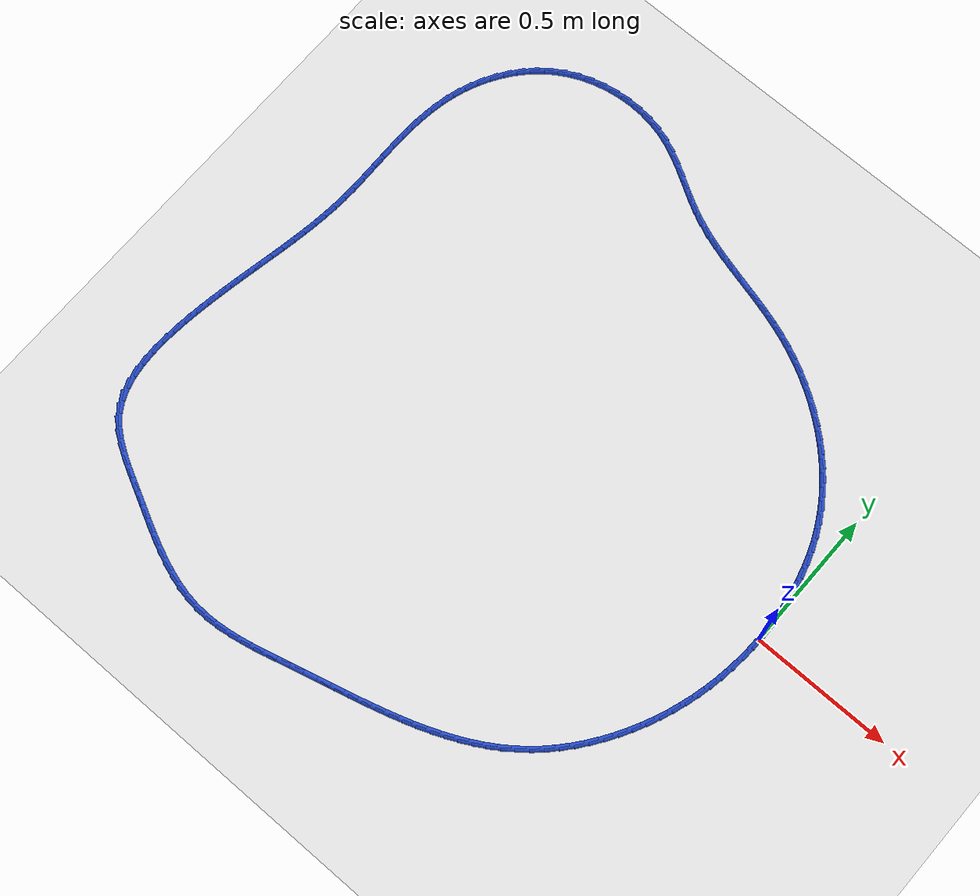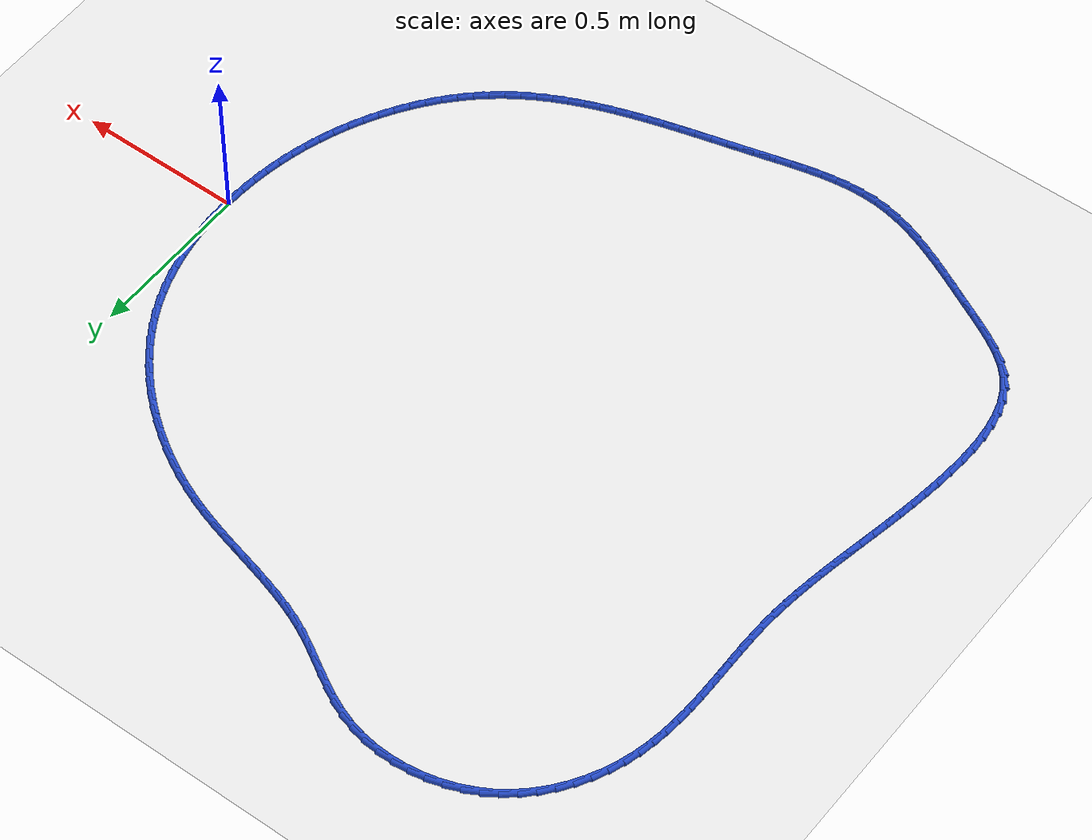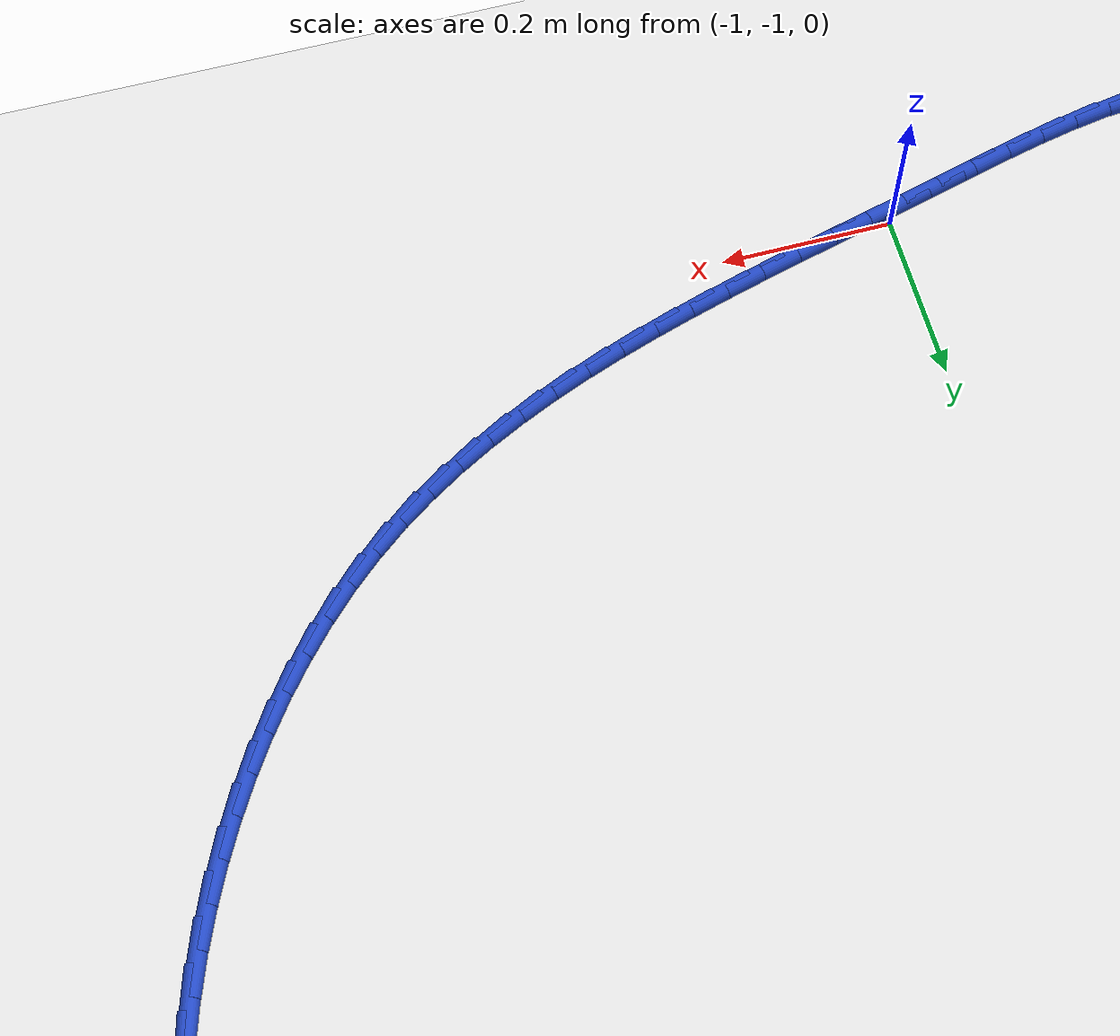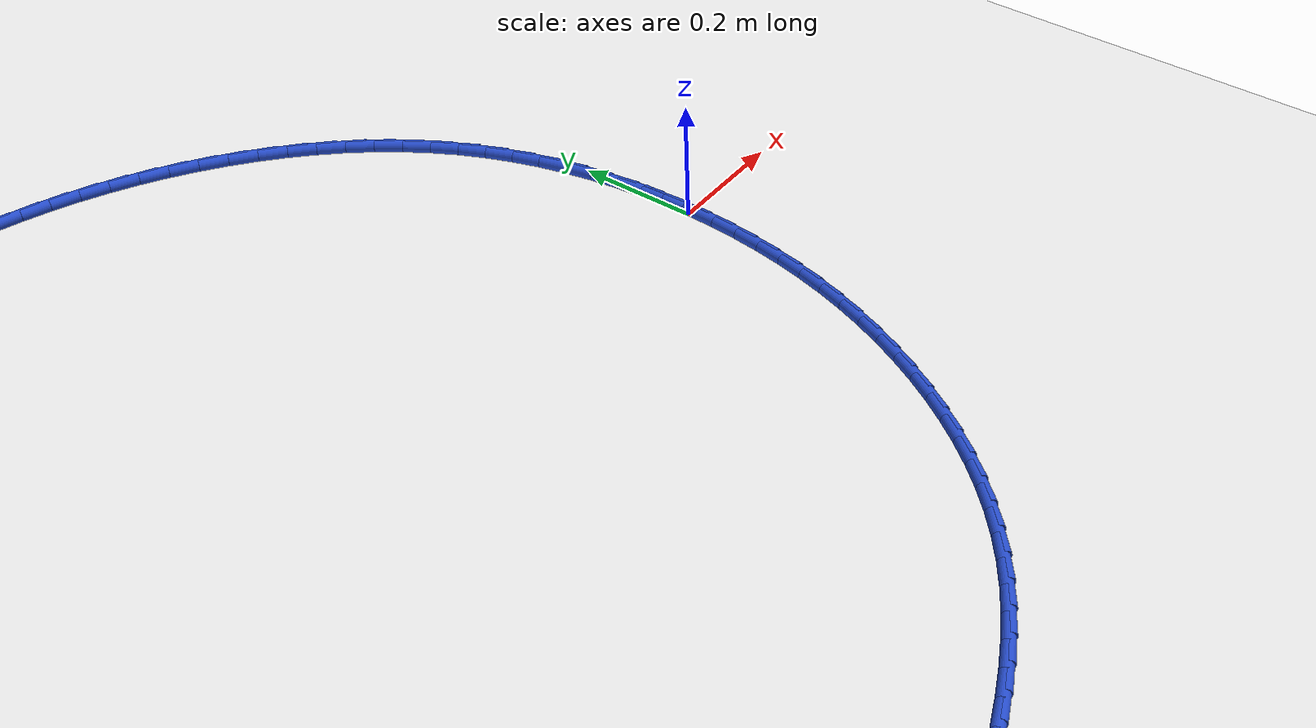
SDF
<sdf version="1.6">
 <world name="default">
  <light name="sun" type="directional">
   <pose>0 0 10 0 -0 0</pose>
   <diffuse>0.8 0.8 0.8 1</diffuse>
   <specular>0.2 0.2 0.2 1</specular>
   <attenuation>
    <range>1000</range>
    <constant>0.9</constant>
    <linear>0.01</linear>
    <quadratic>0.001</quadratic>
   </attenuation>
   <direction>-0.5 0.1 -0.9</direction>
  </light>
  <model name="ground_plane">
   <static>1</static>
   <link name="link">
    <collision name="collision">
     <geometry><plane><normal>0 0 1</normal><size>100 100</size></plane></geometry>
     <surface><friction><ode><mu>100</mu><mu2>50</mu2></ode></friction></surface>
    </collision>
    <visual name="visual">
     <cast_shadows>0</cast_shadows>
     <geometry><plane><normal>0 0 1</normal><size>100 100</size></plane></geometry>
     <material>
      <script><uri>file://media/materials/scripts/gazebo.material</uri><name>Gazebo/WhiteGlow</name></script>
     </material>
    </visual>
   </link>
  </model>
  <gravity>0 0 -9.8</gravity>
  <magnetic_field>6e-06 2.3e-05 -4.2e-05</magnetic_field>
  <atmosphere type="adiabatic"/>
  <physics name="default_physics" default="0" type="ode">
   <max_step_size>0.001</max_step_size>
   <real_time_factor>1</real_time_factor>
   <real_time_update_rate>1000</real_time_update_rate>
  </physics>
  <scene><ambient>0.4 0.4 0.4 1</ambient><background>0.7 0.7 0.7 1</background><shadows>1</shadows></scene>
  <spherical_coordinates>
   <surface_model>EARTH_WGS84</surface_model>
   <latitude_deg>0</latitude_deg>
   <longitude_deg>0</longitude_deg>
   <elevation>0</elevation>
   <heading_deg>0</heading_deg>
  </spherical_coordinates>
  <model name="line">
   <link name="link_0">
    <pose>2.949029909160572e-17 2.7755575615628914e-17 0.01 0 1.57 -1.559873761701563</pose>
    <collision name="collision">
     <geometry><cylinder><radius>0.01</radius><length>0.08</length></cylinder></geometry>
    </collision>
    <visual name="visual">
     <material>
      <script><name>Gazebo/Blue</name><uri>file://media/materials/scripts/gazebo.material</uri></script>
     </material>
     <geometry><cylinder><radius>0.01</radius><length>0.08</length></cylinder></geometry>
    </visual>
   </link>
   <link name="link_1">
    <pose>-0.0005094402092433176 0.04663922307423915 0.01 0 1.57 -1.5152314044498096</pose>
    <collision name="collision">
     <geometry><cylinder><radius>0.01</radius><length>0.08</length></cylinder></geometry>
    </collision>
    <visual name="visual">
     <material>
      <script><name>Gazebo/Blue</name><uri>file://media/materials/scripts/gazebo.material</uri></script>
     </material>
     <geometry><cylinder><radius>0.01</radius><length>0.08</length></cylinder></geometry>
    </visual>
   </link>
   <link name="link_2">
    <pose>-0.0031033703815959756 0.0932740416064086 0.01 0 1.57 -1.4688038409644482</pose>
    <collision name="collision">
     <geometry><cylinder><radius>0.01</radius><length>0.08</length></cylinder></geometry>
    </collision>
    <visual name="visual">
     <material>
      <script><name>Gazebo/Blue</name><uri>file://media/materials/scripts/gazebo.material</uri></script>
     </material>
     <geometry><cylinder><radius>0.01</radius><length>0.08</length></cylinder></geometry>
    </visual>
   </link>
   <link name="link_3">
    <pose>-0.007859479013375437 0.13974418487454873 0.01 0 1.57 -1.4203342513550217</pose>
    <collision name="collision">
     <geometry><cylinder><radius>0.01</radius><length>0.08</length></cylinder></geometry>
    </collision>
    <visual name="visual">
     <material>
      <script><name>Gazebo/Blue</name><uri>file://media/materials/scripts/gazebo.material</uri></script>
     </material>
     <geometry><cylinder><radius>0.01</radius><length>0.08</length></cylinder></geometry>
    </visual>
   </link>
   <link name="link_4">
    <pose>-0.014855454600899176 0.1858893821566998 0.01 0 1.57 -1.3695808221133632</pose>
    <collision name="collision">
     <geometry><cylinder><radius>0.01</radius><length>0.08</length></cylinder></geometry>
    </collision>
    <visual name="visual">
     <material>
      <script><name>Gazebo/Blue</name><uri>file://media/materials/scripts/gazebo.material</uri></script>
     </material>
     <geometry><cylinder><radius>0.01</radius><length>0.08</length></cylinder></geometry>
    </visual>
   </link>
   <link name="link_5">
    <pose>-0.02416898564048467 0.23154936273090207 0.01 0 1.57 -1.3163240880899818</pose>
    <collision name="collision">
     <geometry><cylinder><radius>0.01</radius><length>0.08</length></cylinder></geometry>
    </collision>
    <visual name="visual">
     <material>
      <script><name>Gazebo/Blue</name><uri>file://media/materials/scripts/gazebo.material</uri></script>
     </material>
     <geometry><cylinder><radius>0.01</radius><length>0.08</length></cylinder></geometry>
    </visual>
   </link>
   <link name="link_6">
    <pose>-0.03587776062844941 0.2765638558751961 0.01 0 1.57 -1.2603771881465995</pose>
    <collision name="collision">
     <geometry><cylinder><radius>0.01</radius><length>0.08</length></cylinder></geometry>
    </collision>
    <visual name="visual">
     <material>
      <script><name>Gazebo/Blue</name><uri>file://media/materials/scripts/gazebo.material</uri></script>
     </material>
     <geometry><cylinder><radius>0.01</radius><length>0.08</length></cylinder></geometry>
    </visual>
   </link>
   <link name="link_7">
    <pose>-0.05005946806111087 0.320772590867622 0.01 0 1.57 -1.2015991073382575</pose>
    <collision name="collision">
     <geometry><cylinder><radius>0.01</radius><length>0.08</length></cylinder></geometry>
    </collision>
    <visual name="visual">
     <material>
      <script><name>Gazebo/Blue</name><uri>file://media/materials/scripts/gazebo.material</uri></script>
     </material>
     <geometry><cylinder><radius>0.01</radius><length>0.08</length></cylinder></geometry>
    </visual>
   </link>
   <link name="link_8">
    <pose>-0.06679179643478654 0.36401529698622015 0.01 0 1.57 -1.1399105968034131</pose>
    <collision name="collision">
     <geometry><cylinder><radius>0.01</radius><length>0.08</length></cylinder></geometry>
    </collision>
    <visual name="visual">
     <material>
      <script><name>Gazebo/Blue</name><uri>file://media/materials/scripts/gazebo.material</uri></script>
     </material>
     <geometry><cylinder><radius>0.01</radius><length>0.08</length></cylinder></geometry>
    </visual>
   </link>
   <link name="link_9">
    <pose>-0.08615243424579389 0.40613170350903094 0.01 0 1.57 -1.0761626621845646</pose>
    <collision name="collision">
     <geometry><cylinder><radius>0.01</radius><length>0.08</length></cylinder></geometry>
    </collision>
    <visual name="visual">
     <material>
      <script><name>Gazebo/Blue</name><uri>file://media/materials/scripts/gazebo.material</uri></script>
     </material>
     <geometry><cylinder><radius>0.01</radius><length>0.08</length></cylinder></geometry>
    </visual>
   </link>
   <link name="link_10">
    <pose>-0.10818252262629881 0.4469769590228987 0.01 0 1.57 -1.0139396222992565</pose>
    <collision name="collision">
     <geometry><cylinder><radius>0.01</radius><length>0.08</length></cylinder></geometry>
    </collision>
    <visual name="visual">
     <material>
      <script><name>Gazebo/Blue</name><uri>file://media/materials/scripts/gazebo.material</uri></script>
     </material>
     <geometry><cylinder><radius>0.01</radius><length>0.08</length></cylinder></geometry>
    </visual>
   </link>
   <link name="link_11">
    <pose>-0.13277047609616938 0.48647064737155543 0.01 0 1.57 -0.9541138990512151</pose>
    <collision name="collision">
     <geometry><cylinder><radius>0.01</radius><length>0.08</length></cylinder></geometry>
    </collision>
    <visual name="visual">
     <material>
      <script><name>Gazebo/Blue</name><uri>file://media/materials/scripts/gazebo.material</uri></script>
     </material>
     <geometry><cylinder><radius>0.01</radius><length>0.08</length></cylinder></geometry>
    </visual>
   </link>
   <link name="link_12">
    <pose>-0.15976482081044469 0.5245491812735166 0.01 0 1.57 -0.896564921033001</pose>
    <collision name="collision">
     <geometry><cylinder><radius>0.01</radius><length>0.08</length></cylinder></geometry>
    </collision>
    <visual name="visual">
     <material>
      <script><name>Gazebo/Blue</name><uri>file://media/materials/scripts/gazebo.material</uri></script>
     </material>
     <geometry><cylinder><radius>0.01</radius><length>0.08</length></cylinder></geometry>
    </visual>
   </link>
   <link name="link_13">
    <pose>-0.18901408280578239 0.5611489734972429 0.01 0 1.57 -0.8411264061034113</pose>
    <collision name="collision">
     <geometry><cylinder><radius>0.01</radius><length>0.08</length></cylinder></geometry>
    </collision>
    <visual name="visual">
     <material>
      <script><name>Gazebo/Blue</name><uri>file://media/materials/scripts/gazebo.material</uri></script>
     </material>
     <geometry><cylinder><radius>0.01</radius><length>0.08</length></cylinder></geometry>
    </visual>
   </link>
   <link name="link_14">
    <pose>-0.22036678811884014 0.596206436811195 0.01 0 1.57 -0.7875982919273846</pose>
    <collision name="collision">
     <geometry><cylinder><radius>0.01</radius><length>0.08</length></cylinder></geometry>
    </collision>
    <visual name="visual">
     <material>
      <script><name>Gazebo/Blue</name><uri>file://media/materials/scripts/gazebo.material</uri></script>
     </material>
     <geometry><cylinder><radius>0.01</radius><length>0.08</length></cylinder></geometry>
    </visual>
   </link>
   <link name="link_15">
    <pose>-0.2536714627862756 0.6296579839838337 0.01 0 1.57 -0.7357564472616916</pose>
    <collision name="collision">
     <geometry><cylinder><radius>0.01</radius><length>0.08</length></cylinder></geometry>
    </collision>
    <visual name="visual">
     <material>
      <script><name>Gazebo/Blue</name><uri>file://media/materials/scripts/gazebo.material</uri></script>
     </material>
     <geometry><cylinder><radius>0.01</radius><length>0.08</length></cylinder></geometry>
    </visual>
   </link>
   <link name="link_16">
    <pose>-0.2887766328447464 0.6614400277836197 0.01 0 1.57 -0.6853601250105635</pose>
    <collision name="collision">
     <geometry><cylinder><radius>0.01</radius><length>0.08</length></cylinder></geometry>
    </collision>
    <visual name="visual">
     <material>
      <script><name>Gazebo/Blue</name><uri>file://media/materials/scripts/gazebo.material</uri></script>
     </material>
     <geometry><cylinder><radius>0.01</radius><length>0.08</length></cylinder></geometry>
    </visual>
   </link>
   <link name="link_17">
    <pose>-0.3255308243309102 0.6914889809790136 0.01 0 1.57 -0.6361573325048</pose>
    <collision name="collision">
     <geometry><cylinder><radius>0.01</radius><length>0.08</length></cylinder></geometry>
    </collision>
    <visual name="visual">
     <material>
      <script><name>Gazebo/Blue</name><uri>file://media/materials/scripts/gazebo.material</uri></script>
     </material>
     <geometry><cylinder><radius>0.01</radius><length>0.08</length></cylinder></geometry>
    </visual>
   </link>
   <link name="link_18">
    <pose>-0.3637825632814248 0.7197412563384763 0.01 0 1.57 -0.5878884042394592</pose>
    <collision name="collision">
     <geometry><cylinder><radius>0.01</radius><length>0.08</length></cylinder></geometry>
    </collision>
    <visual name="visual">
     <material>
      <script><name>Gazebo/Blue</name><uri>file://media/materials/scripts/gazebo.material</uri></script>
     </material>
     <geometry><cylinder><radius>0.01</radius><length>0.08</length></cylinder></geometry>
    </visual>
   </link>
   <link name="link_19">
    <pose>-0.40338037573294766 0.7461332666304686 0.01 0 1.57 -0.5402881001267775</pose>
    <collision name="collision">
     <geometry><cylinder><radius>0.01</radius><length>0.08</length></cylinder></geometry>
    </collision>
    <visual name="visual">
     <material>
      <script><name>Gazebo/Blue</name><uri>file://media/materials/scripts/gazebo.material</uri></script>
     </material>
     <geometry><cylinder><radius>0.01</radius><length>0.08</length></cylinder></geometry>
    </visual>
   </link>
   <link name="link_20">
    <pose>-0.44417278772213636 0.7706014246234509 0.01 0 1.57 -0.49308654905106925</pose>
    <collision name="collision">
     <geometry><cylinder><radius>0.01</radius><length>0.08</length></cylinder></geometry>
    </collision>
    <visual name="visual">
     <material>
      <script><name>Gazebo/Blue</name><uri>file://media/materials/scripts/gazebo.material</uri></script>
     </material>
     <geometry><cylinder><radius>0.01</radius><length>0.08</length></cylinder></geometry>
    </visual>
   </link>
   <link name="link_21">
    <pose>-0.48600832528564897 0.7930821430858844 0.01 0 1.57 -0.4460093365763574</pose>
    <collision name="collision">
     <geometry><cylinder><radius>0.01</radius><length>0.08</length></cylinder></geometry>
    </collision>
    <visual name="visual">
     <material>
      <script><name>Gazebo/Blue</name><uri>file://media/materials/scripts/gazebo.material</uri></script>
     </material>
     <geometry><cylinder><radius>0.01</radius><length>0.08</length></cylinder></geometry>
    </visual>
   </link>
   <link name="link_22">
    <pose>-0.5287355144601427 0.8135118347862293 0.01 0 1.57 -0.3987770134314286</pose>
    <collision name="collision">
     <geometry><cylinder><radius>0.01</radius><length>0.08</length></cylinder></geometry>
    </collision>
    <visual name="visual">
     <material>
      <script><name>Gazebo/Blue</name><uri>file://media/materials/scripts/gazebo.material</uri></script>
     </material>
     <geometry><cylinder><radius>0.01</radius><length>0.08</length></cylinder></geometry>
    </visual>
   </link>
   <link name="link_23">
    <pose>-0.5722028812822753 0.8318269124929463 0.01 0 1.57 -0.3520083419137546</pose>
    <collision name="collision">
     <geometry><cylinder><radius>0.01</radius><length>0.08</length></cylinder></geometry>
    </collision>
    <visual name="visual">
     <material>
      <script><name>Gazebo/Blue</name><uri>file://media/materials/scripts/gazebo.material</uri></script>
     </material>
     <geometry><cylinder><radius>0.01</radius><length>0.08</length></cylinder></geometry>
    </visual>
   </link>
   <link name="link_24">
    <pose>-0.6162590524155134 0.8480090134506546 0.01 0 1.57 -0.3121959310141476</pose>
    <collision name="collision">
     <geometry><cylinder><radius>0.01</radius><length>0.08</length></cylinder></geometry>
    </collision>
    <visual name="visual">
     <material>
      <script><name>Gazebo/Blue</name><uri>file://media/materials/scripts/gazebo.material</uri></script>
     </material>
     <geometry><cylinder><radius>0.01</radius><length>0.08</length></cylinder></geometry>
    </visual>
   </link>
   <link name="link_25">
    <pose>-0.6607533883594837 0.8623695812081973 0.01 0 1.57 -0.2824582008621954</pose>
    <collision name="collision">
     <geometry><cylinder><radius>0.01</radius><length>0.08</length></cylinder></geometry>
    </collision>
    <visual name="visual">
     <material>
      <script><name>Gazebo/Blue</name><uri>file://media/materials/scripts/gazebo.material</uri></script>
     </material>
     <geometry><cylinder><radius>0.01</radius><length>0.08</length></cylinder></geometry>
    </visual>
   </link>
   <link name="link_26">
    <pose>-0.7055355747027765 0.8753661633025024 0.01 0 1.57 -0.2629329850610255</pose>
    <collision name="collision">
     <geometry><cylinder><radius>0.01</radius><length>0.08</length></cylinder></geometry>
    </collision>
    <visual name="visual">
     <material>
      <script><name>Gazebo/Blue</name><uri>file://media/materials/scripts/gazebo.material</uri></script>
     </material>
     <geometry><cylinder><radius>0.01</radius><length>0.08</length></cylinder></geometry>
    </visual>
   </link>
   <link name="link_27">
    <pose>-0.7504552984873432 0.8874569604510413 0.01 0 1.57 -0.2536880923601898</pose>
    <collision name="collision">
     <geometry><cylinder><radius>0.01</radius><length>0.08</length></cylinder></geometry>
    </collision>
    <visual name="visual">
     <material>
      <script><name>Gazebo/Blue</name><uri>file://media/materials/scripts/gazebo.material</uri></script>
     </material>
     <geometry><cylinder><radius>0.01</radius><length>0.08</length></cylinder></geometry>
    </visual>
   </link>
   <link name="link_28">
    <pose>-0.7953622467551341 0.8991001733712846 0.01 0 1.57 -0.25479561169535525</pose>
    <collision name="collision">
     <geometry><cylinder><radius>0.01</radius><length>0.08</length></cylinder></geometry>
    </collision>
    <visual name="visual">
     <material>
      <script><name>Gazebo/Blue</name><uri>file://media/materials/scripts/gazebo.material</uri></script>
     </material>
     <geometry><cylinder><radius>0.01</radius><length>0.08</length></cylinder></geometry>
    </visual>
   </link>
   <link name="link_29">
    <pose>-0.8401061065481009 0.9107540027807034 0.01 0 1.57 -0.2663620041468044</pose>
    <collision name="collision">
     <geometry><cylinder><radius>0.01</radius><length>0.08</length></cylinder></geometry>
    </collision>
    <visual name="visual">
     <material>
      <script><name>Gazebo/Blue</name><uri>file://media/materials/scripts/gazebo.material</uri></script>
     </material>
     <geometry><cylinder><radius>0.01</radius><length>0.08</length></cylinder></geometry>
    </visual>
   </link>
   <link name="link_30">
    <pose>-0.8845365649081939 0.9228766493967682 0.01 0 1.57 -0.2885254362625671</pose>
    <collision name="collision">
     <geometry><cylinder><radius>0.01</radius><length>0.08</length></cylinder></geometry>
    </collision>
    <visual name="visual">
     <material>
      <script><name>Gazebo/Blue</name><uri>file://media/materials/scripts/gazebo.material</uri></script>
     </material>
     <geometry><cylinder><radius>0.01</radius><length>0.08</length></cylinder></geometry>
    </visual>
   </link>
   <link name="link_31">
    <pose>-0.9285033088773648 0.9359263139369507 0.01 0 1.57 -0.32141789425308925</pose>
    <collision name="collision">
     <geometry><cylinder><radius>0.01</radius><length>0.08</length></cylinder></geometry>
    </collision>
    <visual name="visual">
     <material>
      <script><name>Gazebo/Blue</name><uri>file://media/materials/scripts/gazebo.material</uri></script>
     </material>
     <geometry><cylinder><radius>0.01</radius><length>0.08</length></cylinder></geometry>
    </visual>
   </link>
   <link name="link_32">
    <pose>-0.9718560254975638 0.9503611971187212 0.01 0 1.57 -0.36508901117233145</pose>
    <collision name="collision">
     <geometry><cylinder><radius>0.01</radius><length>0.08</length></cylinder></geometry>
    </collision>
    <visual name="visual">
     <material>
      <script><name>Gazebo/Blue</name><uri>file://media/materials/scripts/gazebo.material</uri></script>
     </material>
     <geometry><cylinder><radius>0.01</radius><length>0.08</length></cylinder></geometry>
    </visual>
   </link>
   <link name="link_33">
    <pose>-1.0144444018107426 0.9666394996595512 0.01 0 1.57 -0.4193912871517451</pose>
    <collision name="collision">
     <geometry><cylinder><radius>0.01</radius><length>0.08</length></cylinder></geometry>
    </collision>
    <visual name="visual">
     <material>
      <script><name>Gazebo/Blue</name><uri>file://media/materials/scripts/gazebo.material</uri></script>
     </material>
     <geometry><cylinder><radius>0.01</radius><length>0.08</length></cylinder></geometry>
    </visual>
   </link>
   <link name="link_34">
    <pose>-1.0561181248588518 0.9852194222769108 0.01 0 1.57 -0.47927693446181163</pose>
    <collision name="collision">
     <geometry><cylinder><radius>0.01</radius><length>0.08</length></cylinder></geometry>
    </collision>
    <visual name="visual">
     <material>
      <script><name>Gazebo/Blue</name><uri>file://media/materials/scripts/gazebo.material</uri></script>
     </material>
     <geometry><cylinder><radius>0.01</radius><length>0.08</length></cylinder></geometry>
    </visual>
   </link>
   <link name="link_35">
    <pose>-1.096803900731695 1.0063635005245362 0.01 0 1.57 -0.5204897207025851</pose>
    <collision name="collision">
     <geometry><cylinder><radius>0.01</radius><length>0.08</length></cylinder></geometry>
    </collision>
    <visual name="visual">
     <material>
      <script><name>Gazebo/Blue</name><uri>file://media/materials/scripts/gazebo.material</uri></script>
     </material>
     <geometry><cylinder><radius>0.01</radius><length>0.08</length></cylinder></geometry>
    </visual>
   </link>
   <link name="link_36">
    <pose>-1.136832297071943 1.0293082687386517 0.01 0 1.57 -0.535731486797322</pose>
    <collision name="collision">
     <geometry><cylinder><radius>0.01</radius><length>0.08</length></cylinder></geometry>
    </collision>
    <visual name="visual">
     <material>
      <script><name>Gazebo/Blue</name><uri>file://media/materials/scripts/gazebo.material</uri></script>
     </material>
     <geometry><cylinder><radius>0.01</radius><length>0.08</length></cylinder></geometry>
    </visual>
   </link>
   <link name="link_37">
    <pose>-1.176665803420045 1.052955116632838 0.01 0 1.57 -0.525424141886662</pose>
    <collision name="collision">
     <geometry><cylinder><radius>0.01</radius><length>0.08</length></cylinder></geometry>
    </collision>
    <visual name="visual">
     <material>
      <script><name>Gazebo/Blue</name><uri>file://media/materials/scripts/gazebo.material</uri></script>
     </material>
     <geometry><cylinder><radius>0.01</radius><length>0.08</length></cylinder></geometry>
    </visual>
   </link>
   <link name="link_38">
    <pose>-1.2167669833444787 1.076205245854128 0.01 0 1.57 -0.4895350120014604</pose>
    <collision name="collision">
     <geometry><cylinder><radius>0.01</radius><length>0.08</length></cylinder></geometry>
    </collision>
    <visual name="visual">
     <material>
      <script><name>Gazebo/Blue</name><uri>file://media/materials/scripts/gazebo.material</uri></script>
     </material>
     <geometry><cylinder><radius>0.01</radius><length>0.08</length></cylinder></geometry>
    </visual>
   </link>
   <link name="link_39">
    <pose>-1.2575984004137213 1.0979598580495549 0.01 0 1.57 -0.4277782058086873</pose>
    <collision name="collision">
     <geometry><cylinder><radius>0.01</radius><length>0.08</length></cylinder></geometry>
    </collision>
    <visual name="visual">
     <material>
      <script><name>Gazebo/Blue</name><uri>file://media/materials/scripts/gazebo.material</uri></script>
     </material>
     <geometry><cylinder><radius>0.01</radius><length>0.08</length></cylinder></geometry>
    </visual>
   </link>
   <link name="link_40">
    <pose>-1.2996226181962505 1.1171201548661513 0.01 0 1.57 -0.34037503169275535</pose>
    <collision name="collision">
     <geometry><cylinder><radius>0.01</radius><length>0.08</length></cylinder></geometry>
    </collision>
    <visual name="visual">
     <material>
      <script><name>Gazebo/Blue</name><uri>file://media/materials/scripts/gazebo.material</uri></script>
     </material>
     <geometry><cylinder><radius>0.01</radius><length>0.08</length></cylinder></geometry>
    </visual>
   </link>
   <link name="link_41">
    <pose>-1.3433006260002136 1.1325891097746126 0.01 0 1.57 -0.23743847597893408</pose>
    <collision name="collision">
     <geometry><cylinder><radius>0.01</radius><length>0.08</length></cylinder></geometry>
    </collision>
    <visual name="visual">
     <material>
      <script><name>Gazebo/Blue</name><uri>file://media/materials/scripts/gazebo.material</uri></script>
     </material>
     <geometry><cylinder><radius>0.01</radius><length>0.08</length></cylinder></geometry>
    </visual>
   </link>
   <link name="link_42">
    <pose>-1.3887998648804614 1.1436000836223037 0.01 0 1.57 -0.13790647263707143</pose>
    <collision name="collision">
     <geometry><cylinder><radius>0.01</radius><length>0.08</length></cylinder></geometry>
    </collision>
    <visual name="visual">
     <material>
      <script><name>Gazebo/Blue</name><uri>file://media/materials/scripts/gazebo.material</uri></script>
     </material>
     <geometry><cylinder><radius>0.01</radius><length>0.08</length></cylinder></geometry>
    </visual>
   </link>
   <link name="link_43">
    <pose>-1.4356515491007282 1.150102507947271 0.01 0 1.57 -0.0427215888527072</pose>
    <collision name="collision">
     <geometry><cylinder><radius>0.01</radius><length>0.08</length></cylinder></geometry>
    </collision>
    <visual name="visual">
     <material>
      <script><name>Gazebo/Blue</name><uri>file://media/materials/scripts/gazebo.material</uri></script>
     </material>
     <geometry><cylinder><radius>0.01</radius><length>0.08</length></cylinder></geometry>
    </visual>
   </link>
   <link name="link_44">
    <pose>-1.4833036354734572 1.1521395202136293 0.01 0 1.57 0.049755147119950674</pose>
    <collision name="collision">
     <geometry><cylinder><radius>0.01</radius><length>0.08</length></cylinder></geometry>
    </collision>
    <visual name="visual">
     <material>
      <script><name>Gazebo/Blue</name><uri>file://media/materials/scripts/gazebo.material</uri></script>
     </material>
     <geometry><cylinder><radius>0.01</radius><length>0.08</length></cylinder></geometry>
    </visual>
   </link>
   <link name="link_45">
    <pose>-1.5312040808110914 1.1497542578854933 0.01 0 1.57 0.14117350452861044</pose>
    <collision name="collision">
     <geometry><cylinder><radius>0.01</radius><length>0.08</length></cylinder></geometry>
    </collision>
    <visual name="visual">
     <material>
      <script><name>Gazebo/Blue</name><uri>file://media/materials/scripts/gazebo.material</uri></script>
     </material>
     <geometry><cylinder><radius>0.01</radius><length>0.08</length></cylinder></geometry>
    </visual>
   </link>
   <link name="link_46">
    <pose>-1.5788008419260717 1.1429898584269773 0.01 0 1.57 0.2331677226443067</pose>
    <collision name="collision">
     <geometry><cylinder><radius>0.01</radius><length>0.08</length></cylinder></geometry>
    </collision>
    <visual name="visual">
     <material>
      <script><name>Gazebo/Blue</name><uri>file://media/materials/scripts/gazebo.material</uri></script>
     </material>
     <geometry><cylinder><radius>0.01</radius><length>0.08</length></cylinder></geometry>
    </visual>
   </link>
   <link name="link_47">
    <pose>-1.6255418756308413 1.131889459302196 0.01 0 1.57 0.32734203992440386</pose>
    <collision name="collision">
     <geometry><cylinder><radius>0.01</radius><length>0.08</length></cylinder></geometry>
    </collision>
    <visual name="visual">
     <material>
      <script><name>Gazebo/Blue</name><uri>file://media/materials/scripts/gazebo.material</uri></script>
     </material>
     <geometry><cylinder><radius>0.01</radius><length>0.08</length></cylinder></geometry>
    </visual>
   </link>
   <link name="link_48">
    <pose>-1.6708751387378422 1.1164961979752634 0.01 0 1.57 0.42524670431014155</pose>
    <collision name="collision">
     <geometry><cylinder><radius>0.01</radius><length>0.08</length></cylinder></geometry>
    </collision>
    <visual name="visual">
     <material>
      <script><name>Gazebo/Blue</name><uri>file://media/materials/scripts/gazebo.material</uri></script>
     </material>
     <geometry><cylinder><radius>0.01</radius><length>0.08</length></cylinder></geometry>
    </visual>
   </link>
   <link name="link_49">
    <pose>-1.7142485880595175 1.096853211910295 0.01 0 1.57 0.5283235539777915</pose>
    <collision name="collision">
     <geometry><cylinder><radius>0.01</radius><length>0.08</length></cylinder></geometry>
    </collision>
    <visual name="visual">
     <material>
      <script><name>Gazebo/Blue</name><uri>file://media/materials/scripts/gazebo.material</uri></script>
     </material>
     <geometry><cylinder><radius>0.01</radius><length>0.08</length></cylinder></geometry>
    </visual>
   </link>
   <link name="link_50">
    <pose>-1.7551101804083091 1.0730036385714044 0.01 0 1.57 0.6357839634131698</pose>
    <collision name="collision">
     <geometry><cylinder><radius>0.01</radius><length>0.08</length></cylinder></geometry>
    </collision>
    <visual name="visual">
     <material>
      <script><name>Gazebo/Blue</name><uri>file://media/materials/scripts/gazebo.material</uri></script>
     </material>
     <geometry><cylinder><radius>0.01</radius><length>0.08</length></cylinder></geometry>
    </visual>
   </link>
   <link name="link_51">
    <pose>-1.7929816792724023 1.0450540515688203 0.01 0 1.57 0.7393848744995453</pose>
    <collision name="collision">
     <geometry><cylinder><radius>0.01</radius><length>0.08</length></cylinder></geometry>
    </collision>
    <visual name="visual">
     <material>
      <script><name>Gazebo/Blue</name><uri>file://media/materials/scripts/gazebo.material</uri></script>
     </material>
     <geometry><cylinder><radius>0.01</radius><length>0.08</length></cylinder></geometry>
    </visual>
   </link>
   <link name="link_52">
    <pose>-1.827705848960537 1.0133869217097409 0.01 0 1.57 0.8368378226469672</pose>
    <collision name="collision">
     <geometry><cylinder><radius>0.01</radius><length>0.08</length></cylinder></geometry>
    </collision>
    <visual name="visual">
     <material>
      <script><name>Gazebo/Blue</name><uri>file://media/materials/scripts/gazebo.material</uri></script>
     </material>
     <geometry><cylinder><radius>0.01</radius><length>0.08</length></cylinder></geometry>
    </visual>
   </link>
   <link name="link_53">
    <pose>-1.8592127002818553 0.9784597073508211 0.01 0 1.57 0.9286167964909425</pose>
    <collision name="collision">
     <geometry><cylinder><radius>0.01</radius><length>0.08</length></cylinder></geometry>
    </collision>
    <visual name="visual">
     <material>
      <script><name>Gazebo/Blue</name><uri>file://media/materials/scripts/gazebo.material</uri></script>
     </material>
     <geometry><cylinder><radius>0.01</radius><length>0.08</length></cylinder></geometry>
    </visual>
   </link>
   <link name="link_54">
    <pose>-1.8874322457880004 0.9407298683463771 0.01 0 1.57 1.015516764488374</pose>
    <collision name="collision">
     <geometry><cylinder><radius>0.01</radius><length>0.08</length></cylinder></geometry>
    </collision>
    <visual name="visual">
     <material>
      <script><name>Gazebo/Blue</name><uri>file://media/materials/scripts/gazebo.material</uri></script>
     </material>
     <geometry><cylinder><radius>0.01</radius><length>0.08</length></cylinder></geometry>
    </visual>
   </link>
   <link name="link_55">
    <pose>-1.9122944980306156 0.9006548645507276 0.01 0 1.57 1.098538158207671</pose>
    <collision name="collision">
     <geometry><cylinder><radius>0.01</radius><length>0.08</length></cylinder></geometry>
    </collision>
    <visual name="visual">
     <material>
      <script><name>Gazebo/Blue</name><uri>file://media/materials/scripts/gazebo.material</uri></script>
     </material>
     <geometry><cylinder><radius>0.01</radius><length>0.08</length></cylinder></geometry>
    </visual>
   </link>
   <link name="link_56">
    <pose>-1.9337294695613434 0.858692155818189 0.01 0 1.57 1.1788104381272797</pose>
    <collision name="collision">
     <geometry><cylinder><radius>0.01</radius><length>0.08</length></cylinder></geometry>
    </collision>
    <visual name="visual">
     <material>
      <script><name>Gazebo/Blue</name><uri>file://media/materials/scripts/gazebo.material</uri></script>
     </material>
     <geometry><cylinder><radius>0.01</radius><length>0.08</length></cylinder></geometry>
    </visual>
   </link>
   <link name="link_57">
    <pose>-1.951667172931827 0.815299202003079 0.01 0 1.57 1.2575298625116862</pose>
    <collision name="collision">
     <geometry><cylinder><radius>0.01</radius><length>0.08</length></cylinder></geometry>
    </collision>
    <visual name="visual">
     <material>
      <script><name>Gazebo/Blue</name><uri>file://media/materials/scripts/gazebo.material</uri></script>
     </material>
     <geometry><cylinder><radius>0.01</radius><length>0.08</length></cylinder></geometry>
    </visual>
   </link>
   <link name="link_58">
    <pose>-1.9660389996991319 0.7709325272063688 0.01 0 1.57 1.3330420297755883</pose>
    <collision name="collision">
     <geometry><cylinder><radius>0.01</radius><length>0.08</length></cylinder></geometry>
    </collision>
    <visual name="visual">
     <material>
      <script><name>Gazebo/Blue</name><uri>file://media/materials/scripts/gazebo.material</uri></script>
     </material>
     <geometry><cylinder><radius>0.01</radius><length>0.08</length></cylinder></geometry>
    </visual>
   </link>
   <link name="link_59">
    <pose>-1.9769435565901758 0.7259351881329419 0.01 0 1.57 1.399739414902737</pose>
    <collision name="collision">
     <geometry><cylinder><radius>0.01</radius><length>0.08</length></cylinder></geometry>
    </collision>
    <visual name="visual">
     <material>
      <script><name>Gazebo/Blue</name><uri>file://media/materials/scripts/gazebo.material</uri></script>
     </material>
     <geometry><cylinder><radius>0.01</radius><length>0.08</length></cylinder></geometry>
    </visual>
   </link>
   <link name="link_60">
    <pose>-1.9848043984560055 0.6804297410537653 0.01 0 1.57 1.4563495433846998</pose>
    <collision name="collision">
     <geometry><cylinder><radius>0.01</radius><length>0.08</length></cylinder></geometry>
    </collision>
    <visual name="visual">
     <material>
      <script><name>Gazebo/Blue</name><uri>file://media/materials/scripts/gazebo.material</uri></script>
     </material>
     <geometry><cylinder><radius>0.01</radius><length>0.08</length></cylinder></geometry>
    </visual>
   </link>
   <link name="link_61">
    <pose>-1.990082441337623 0.6345133900128358 0.01 0 1.57 1.5026313555036652</pose>
    <collision name="collision">
     <geometry><cylinder><radius>0.01</radius><length>0.08</length></cylinder></geometry>
    </collision>
    <visual name="visual">
     <material>
      <script><name>Gazebo/Blue</name><uri>file://media/materials/scripts/gazebo.material</uri></script>
     </material>
     <geometry><cylinder><radius>0.01</radius><length>0.08</length></cylinder></geometry>
    </visual>
   </link>
   <link name="link_62">
    <pose>-1.9932386012760326 0.5882833390541492 0.01 0 1.57 1.5386157457409615</pose>
    <collision name="collision">
     <geometry><cylinder><radius>0.01</radius><length>0.08</length></cylinder></geometry>
    </collision>
    <visual name="visual">
     <material>
      <script><name>Gazebo/Blue</name><uri>file://media/materials/scripts/gazebo.material</uri></script>
     </material>
     <geometry><cylinder><radius>0.01</radius><length>0.08</length></cylinder></geometry>
    </visual>
   </link>
   <link name="link_63">
    <pose>-1.9947337943122376 0.5418367922217022 0.01 0 1.57 1.5644582422378988</pose>
    <collision name="collision">
     <geometry><cylinder><radius>0.01</radius><length>0.08</length></cylinder></geometry>
    </collision>
    <visual name="visual">
     <material>
      <script><name>Gazebo/Blue</name><uri>file://media/materials/scripts/gazebo.material</uri></script>
     </material>
     <geometry><cylinder><radius>0.01</radius><length>0.08</length></cylinder></geometry>
    </visual>
   </link>
   <link name="link_64">
    <pose>-1.99502893648724 0.495270953559491 0.01 0 1.57 -1.5612664069654179</pose>
    <collision name="collision">
     <geometry><cylinder><radius>0.01</radius><length>0.08</length></cylinder></geometry>
    </collision>
    <visual name="visual">
     <material>
      <script><name>Gazebo/Blue</name><uri>file://media/materials/scripts/gazebo.material</uri></script>
     </material>
     <geometry><cylinder><radius>0.01</radius><length>0.08</length></cylinder></geometry>
    </visual>
   </link>
   <link name="link_65">
    <pose>-1.9945849438420433 0.44868302711151153 0.01 0 1.57 -1.5552704235019725</pose>
    <collision name="collision">
     <geometry><cylinder><radius>0.01</radius><length>0.08</length></cylinder></geometry>
    </collision>
    <visual name="visual">
     <material>
      <script><name>Gazebo/Blue</name><uri>file://media/materials/scripts/gazebo.material</uri></script>
     </material>
     <geometry><cylinder><radius>0.01</radius><length>0.08</length></cylinder></geometry>
    </visual>
   </link>
   <link name="link_66">
    <pose>-1.9938627324176503 0.4021702169217602 0.01 0 1.57 -1.5591544604772611</pose>
    <collision name="collision">
     <geometry><cylinder><radius>0.01</radius><length>0.08</length></cylinder></geometry>
    </collision>
    <visual name="visual">
     <material>
      <script><name>Gazebo/Blue</name><uri>file://media/materials/scripts/gazebo.material</uri></script>
     </material>
     <geometry><cylinder><radius>0.01</radius><length>0.08</length></cylinder></geometry>
    </visual>
   </link>
   <link name="link_67">
    <pose>-1.9933232182550655 0.3558297270342329 0.01 0 1.57 1.5685367917093591</pose>
    <collision name="collision">
     <geometry><cylinder><radius>0.01</radius><length>0.08</length></cylinder></geometry>
    </collision>
    <visual name="visual">
     <material>
      <script><name>Gazebo/Blue</name><uri>file://media/materials/scripts/gazebo.material</uri></script>
     </material>
     <geometry><cylinder><radius>0.01</radius><length>0.08</length></cylinder></geometry>
    </visual>
   </link>
   <link name="link_68">
    <pose>-1.99342731739529 0.30975876149292647 0.01 0 1.57 1.5443579276386854</pose>
    <collision name="collision">
     <geometry><cylinder><radius>0.01</radius><length>0.08</length></cylinder></geometry>
    </collision>
    <visual name="visual">
     <material>
      <script><name>Gazebo/Blue</name><uri>file://media/materials/scripts/gazebo.material</uri></script>
     </material>
     <geometry><cylinder><radius>0.01</radius><length>0.08</length></cylinder></geometry>
    </visual>
   </link>
   <link name="link_69">
    <pose>-1.9946359458793292 0.26405452434183685 0.01 0 1.57 1.5112020425151593</pose>
    <collision name="collision">
     <geometry><cylinder><radius>0.01</radius><length>0.08</length></cylinder></geometry>
    </collision>
    <visual name="visual">
     <material>
      <script><name>Gazebo/Blue</name><uri>file://media/materials/scripts/gazebo.material</uri></script>
     </material>
     <geometry><cylinder><radius>0.01</radius><length>0.08</length></cylinder></geometry>
    </visual>
   </link>
   <link name="link_70">
    <pose>-1.9973365516080612 0.21879166136424308 0.01 0 1.57 1.4784598613704998</pose>
    <collision name="collision">
     <geometry><cylinder><radius>0.01</radius><length>0.08</length></cylinder></geometry>
    </collision>
    <visual name="visual">
     <material>
      <script><name>Gazebo/Blue</name><uri>file://media/materials/scripts/gazebo.material</uri></script>
     </material>
     <geometry><cylinder><radius>0.01</radius><length>0.08</length></cylinder></geometry>
    </visual>
   </link>
   <link name="link_71">
    <pose>-2.0014921668640357 0.17391450228867214 0.01 0 1.57 1.4498128613974492</pose>
    <collision name="collision">
     <geometry><cylinder><radius>0.01</radius><length>0.08</length></cylinder></geometry>
    </collision>
    <visual name="visual">
     <material>
      <script><name>Gazebo/Blue</name><uri>file://media/materials/scripts/gazebo.material</uri></script>
     </material>
     <geometry><cylinder><radius>0.01</radius><length>0.08</length></cylinder></geometry>
    </visual>
   </link>
   <link name="link_72">
    <pose>-2.0069137591343513 0.1293206856208188 0.01 0 1.57 1.4255106887678506</pose>
    <collision name="collision">
     <geometry><cylinder><radius>0.01</radius><length>0.08</length></cylinder></geometry>
    </collision>
    <visual name="visual">
     <material>
      <script><name>Gazebo/Blue</name><uri>file://media/materials/scripts/gazebo.material</uri></script>
     </material>
     <geometry><cylinder><radius>0.01</radius><length>0.08</length></cylinder></geometry>
    </visual>
   </link>
   <link name="link_73">
    <pose>-2.013412101607723 0.08490779020740581 0.01 0 1.57 1.4057178785920594</pose>
    <collision name="collision">
     <geometry><cylinder><radius>0.01</radius><length>0.08</length></cylinder></geometry>
    </collision>
    <visual name="visual">
     <material>
      <script><name>Gazebo/Blue</name><uri>file://media/materials/scripts/gazebo.material</uri></script>
     </material>
     <geometry><cylinder><radius>0.01</radius><length>0.08</length></cylinder></geometry>
    </visual>
   </link>
   <link name="link_74">
    <pose>-2.020797967472865 0.0405733948951564 0.01 0 1.57 1.3905279289799297</pose>
    <collision name="collision">
     <geometry><cylinder><radius>0.01</radius><length>0.08</length></cylinder></geometry>
    </collision>
    <visual name="visual">
     <material>
      <script><name>Gazebo/Blue</name><uri>file://media/materials/scripts/gazebo.material</uri></script>
     </material>
     <geometry><cylinder><radius>0.01</radius><length>0.08</length></cylinder></geometry>
    </visual>
   </link>
   <link name="link_75">
    <pose>-2.028882129918492 -0.003784921469206167 0.01 0 1.57 1.379973784292877</pose>
    <collision name="collision">
     <geometry><cylinder><radius>0.01</radius><length>0.08</length></cylinder></geometry>
    </collision>
    <visual name="visual">
     <material>
      <script><name>Gazebo/Blue</name><uri>file://media/materials/scripts/gazebo.material</uri></script>
     </material>
     <geometry><cylinder><radius>0.01</radius><length>0.08</length></cylinder></geometry>
    </visual>
   </link>
   <link name="link_76">
    <pose>-2.0374753621333186 -0.04826958003895916 0.01 0 1.57 1.374037578399826</pose>
    <collision name="collision">
     <geometry><cylinder><radius>0.01</radius><length>0.08</length></cylinder></geometry>
    </collision>
    <visual name="visual">
     <material>
      <script><name>Gazebo/Blue</name><uri>file://media/materials/scripts/gazebo.material</uri></script>
     </material>
     <geometry><cylinder><radius>0.01</radius><length>0.08</length></cylinder></geometry>
    </visual>
   </link>
   <link name="link_77">
    <pose>-2.046388437306059 -0.09298300196737896 0.01 0 1.57 1.3726586635768854</pose>
    <collision name="collision">
     <geometry><cylinder><radius>0.01</radius><length>0.08</length></cylinder></geometry>
    </collision>
    <visual name="visual">
     <material>
      <script><name>Gazebo/Blue</name><uri>file://media/materials/scripts/gazebo.material</uri></script>
     </material>
     <geometry><cylinder><radius>0.01</radius><length>0.08</length></cylinder></geometry>
    </visual>
   </link>
   <link name="link_78">
    <pose>-2.0554321286254273 -0.13802760840774167 0.01 0 1.57 1.3757394455502725</pose>
    <collision name="collision">
     <geometry><cylinder><radius>0.01</radius><length>0.08</length></cylinder></geometry>
    </collision>
    <visual name="visual">
     <material>
      <script><name>Gazebo/Blue</name><uri>file://media/materials/scripts/gazebo.material</uri></script>
     </material>
     <geometry><cylinder><radius>0.01</radius><length>0.08</length></cylinder></geometry>
    </visual>
   </link>
   <link name="link_79">
    <pose>-2.064417209280139 -0.18350582051332553 0.01 0 1.57 1.3831489538576112</pose>
    <collision name="collision">
     <geometry><cylinder><radius>0.01</radius><length>0.08</length></cylinder></geometry>
    </collision>
    <visual name="visual">
     <material>
      <script><name>Gazebo/Blue</name><uri>file://media/materials/scripts/gazebo.material</uri></script>
     </material>
     <geometry><cylinder><radius>0.01</radius><length>0.08</length></cylinder></geometry>
    </visual>
   </link>
   <link name="link_80">
    <pose>-2.0731544524589083 -0.2295200594374059 0.01 0 1.57 1.3947243905979094</pose>
    <collision name="collision">
     <geometry><cylinder><radius>0.01</radius><length>0.08</length></cylinder></geometry>
    </collision>
    <visual name="visual">
     <material>
      <script><name>Gazebo/Blue</name><uri>file://media/materials/scripts/gazebo.material</uri></script>
     </material>
     <geometry><cylinder><radius>0.01</radius><length>0.08</length></cylinder></geometry>
    </visual>
   </link>
   <link name="link_81">
    <pose>-2.081454631350449 -0.2761727463332611 0.01 0 1.57 1.4102711315188607</pose>
    <collision name="collision">
     <geometry><cylinder><radius>0.01</radius><length>0.08</length></cylinder></geometry>
    </collision>
    <visual name="visual">
     <material>
      <script><name>Gazebo/Blue</name><uri>file://media/materials/scripts/gazebo.material</uri></script>
     </material>
     <geometry><cylinder><radius>0.01</radius><length>0.08</length></cylinder></geometry>
    </visual>
   </link>
   <link name="link_82">
    <pose>-2.089128519143477 -0.32356630235416717 0.01 0 1.57 1.4295618158417176</pose>
    <collision name="collision">
     <geometry><cylinder><radius>0.01</radius><length>0.08</length></cylinder></geometry>
    </collision>
    <visual name="visual">
     <material>
      <script><name>Gazebo/Blue</name><uri>file://media/materials/scripts/gazebo.material</uri></script>
     </material>
     <geometry><cylinder><radius>0.01</radius><length>0.08</length></cylinder></geometry>
    </visual>
   </link>
   <link name="link_83">
    <pose>-2.0959868890267055 -0.37180314865340003 0.01 0 1.57 1.4524372828955616</pose>
    <collision name="collision">
     <geometry><cylinder><radius>0.01</radius><length>0.08</length></cylinder></geometry>
    </collision>
    <visual name="visual">
     <material>
      <script><name>Gazebo/Blue</name><uri>file://media/materials/scripts/gazebo.material</uri></script>
     </material>
     <geometry><cylinder><radius>0.01</radius><length>0.08</length></cylinder></geometry>
    </visual>
   </link>
   <link name="link_84">
    <pose>-2.1018341569673336 -0.42097503859744667 0.01 0 1.57 1.4819904620774775</pose>
    <collision name="collision">
     <geometry><cylinder><radius>0.01</radius><length>0.08</length></cylinder></geometry>
    </collision>
    <visual name="visual">
     <material>
      <script><name>Gazebo/Blue</name><uri>file://media/materials/scripts/gazebo.material</uri></script>
     </material>
     <geometry><cylinder><radius>0.01</radius><length>0.08</length></cylinder></geometry>
    </visual>
   </link>
   <link name="link_85">
    <pose>-2.1062738327281667 -0.47083659327761146 0.01 0 1.57 1.5227731970459915</pose>
    <collision name="collision">
     <geometry><cylinder><radius>0.01</radius><length>0.08</length></cylinder></geometry>
    </collision>
    <visual name="visual">
     <material>
      <script><name>Gazebo/Blue</name><uri>file://media/materials/scripts/gazebo.material</uri></script>
     </material>
     <geometry><cylinder><radius>0.01</radius><length>0.08</length></cylinder></geometry>
    </visual>
   </link>
   <link name="link_86">
    <pose>-2.1086724216674977 -0.520744726634435 0.01 0 1.57 -1.564920179285367</pose>
    <collision name="collision">
     <geometry><cylinder><radius>0.01</radius><length>0.08</length></cylinder></geometry>
    </collision>
    <visual name="visual">
     <material>
      <script><name>Gazebo/Blue</name><uri>file://media/materials/scripts/gazebo.material</uri></script>
     </material>
     <geometry><cylinder><radius>0.01</radius><length>0.08</length></cylinder></geometry>
    </visual>
   </link>
   <link name="link_87">
    <pose>-2.1083827904305203 -0.5700334660560372 0.01 0 1.57 -1.495424170975632</pose>
    <collision name="collision">
     <geometry><cylinder><radius>0.01</radius><length>0.08</length></cylinder></geometry>
    </collision>
    <visual name="visual">
     <material>
      <script><name>Gazebo/Blue</name><uri>file://media/materials/scripts/gazebo.material</uri></script>
     </material>
     <geometry><cylinder><radius>0.01</radius><length>0.08</length></cylinder></geometry>
    </visual>
   </link>
   <link name="link_88">
    <pose>-2.1047578056624285 -0.6180368389305375 0.01 0 1.57 -1.407081870216652</pose>
    <collision name="collision">
     <geometry><cylinder><radius>0.01</radius><length>0.08</length></cylinder></geometry>
    </collision>
    <visual name="visual">
     <material>
      <script><name>Gazebo/Blue</name><uri>file://media/materials/scripts/gazebo.material</uri></script>
     </material>
     <geometry><cylinder><radius>0.01</radius><length>0.08</length></cylinder></geometry>
    </visual>
   </link>
   <link name="link_89">
    <pose>-2.0971503340084148 -0.6640888726460586 0.01 0 1.57 -1.2961792604196254</pose>
    <collision name="collision">
     <geometry><cylinder><radius>0.01</radius><length>0.08</length></cylinder></geometry>
    </collision>
    <visual name="visual">
     <material>
      <script><name>Gazebo/Blue</name><uri>file://media/materials/scripts/gazebo.material</uri></script>
     </material>
     <geometry><cylinder><radius>0.01</radius><length>0.08</length></cylinder></geometry>
    </visual>
   </link>
   <link name="link_90">
    <pose>-2.084913242113674 -0.7075235945907203 0.01 0 1.57 -1.1594819805172856</pose>
    <collision name="collision">
     <geometry><cylinder><radius>0.01</radius><length>0.08</length></cylinder></geometry>
    </collision>
    <visual name="visual">
     <material>
      <script><name>Gazebo/Blue</name><uri>file://media/materials/scripts/gazebo.material</uri></script>
     </material>
     <geometry><cylinder><radius>0.01</radius><length>0.08</length></cylinder></geometry>
    </visual>
   </link>
   <link name="link_91">
    <pose>-2.0673993966233972 -0.7476750321526421 0.01 0 1.57 -0.9962473769882602</pose>
    <collision name="collision">
     <geometry><cylinder><radius>0.01</radius><length>0.08</length></cylinder></geometry>
    </collision>
    <visual name="visual">
     <material>
      <script><name>Gazebo/Blue</name><uri>file://media/materials/scripts/gazebo.material</uri></script>
     </material>
     <geometry><cylinder><radius>0.01</radius><length>0.08</length></cylinder></geometry>
    </visual>
   </link>
   <link name="link_92">
    <pose>-2.043961829288558 -0.78387734729675 0.01 0 1.57 -0.8225497552959556</pose>
    <collision name="collision">
     <geometry><cylinder><radius>0.01</radius><length>0.08</length></cylinder></geometry>
    </collision>
    <visual name="visual">
     <material>
      <script><name>Gazebo/Blue</name><uri>file://media/materials/scripts/gazebo.material</uri></script>
     </material>
     <geometry><cylinder><radius>0.01</radius><length>0.08</length></cylinder></geometry>
    </visual>
   </link>
   <link name="link_93">
    <pose>-2.0143434423365263 -0.8157824832487682 0.01 0 1.57 -0.6815727432666651</pose>
    <collision name="collision">
     <geometry><cylinder><radius>0.01</radius><length>0.08</length></cylinder></geometry>
    </collision>
    <visual name="visual">
     <material>
      <script><name>Gazebo/Blue</name><uri>file://media/materials/scripts/gazebo.material</uri></script>
     </material>
     <geometry><cylinder><radius>0.01</radius><length>0.08</length></cylinder></geometry>
    </visual>
   </link>
   <link name="link_94">
    <pose>-1.9795115593122141 -0.8440404022525272 0.01 0 1.57 -0.5801881097216998</pose>
    <collision name="collision">
     <geometry><cylinder><radius>0.01</radius><length>0.08</length></cylinder></geometry>
    </collision>
    <visual name="visual">
     <material>
      <script><name>Gazebo/Blue</name><uri>file://media/materials/scripts/gazebo.material</uri></script>
     </material>
     <geometry><cylinder><radius>0.01</radius><length>0.08</length></cylinder></geometry>
    </visual>
   </link>
   <link name="link_95">
    <pose>-1.940673248570413 -0.8694964812153552 0.01 0 1.57 -0.5138191316384008</pose>
    <collision name="collision">
     <geometry><cylinder><radius>0.01</radius><length>0.08</length></cylinder></geometry>
    </collision>
    <visual name="visual">
     <material>
      <script><name>Gazebo/Blue</name><uri>file://media/materials/scripts/gazebo.material</uri></script>
     </material>
     <geometry><cylinder><radius>0.01</radius><length>0.08</length></cylinder></geometry>
    </visual>
   </link>
   <link name="link_96">
    <pose>-1.8990355784659174 -0.8929960970445827 0.01 0 1.57 -0.47785997398480323</pose>
    <collision name="collision">
     <geometry><cylinder><radius>0.01</radius><length>0.08</length></cylinder></geometry>
    </collision>
    <visual name="visual">
     <material>
      <script><name>Gazebo/Blue</name><uri>file://media/materials/scripts/gazebo.material</uri></script>
     </material>
     <geometry><cylinder><radius>0.01</radius><length>0.08</length></cylinder></geometry>
    </visual>
   </link>
   <link name="link_97">
    <pose>-1.8558056173535187 -0.9153846266475403 0.01 0 1.57 -0.46911303428842643</pose>
    <collision name="collision">
     <geometry><cylinder><radius>0.01</radius><length>0.08</length></cylinder></geometry>
    </collision>
    <visual name="visual">
     <material>
      <script><name>Gazebo/Blue</name><uri>file://media/materials/scripts/gazebo.material</uri></script>
     </material>
     <geometry><cylinder><radius>0.01</radius><length>0.08</length></cylinder></geometry>
    </visual>
   </link>
   <link name="link_98">
    <pose>-1.8121796110334112 -0.9374964928378228 0.01 0 1.57 -0.4725597588904915</pose>
    <collision name="collision">
     <geometry><cylinder><radius>0.01</radius><length>0.08</length></cylinder></geometry>
    </collision>
    <visual name="visual">
     <material>
      <script><name>Gazebo/Blue</name><uri>file://media/materials/scripts/gazebo.material</uri></script>
     </material>
     <geometry><cylinder><radius>0.01</radius><length>0.08</length></cylinder></geometry>
    </visual>
   </link>
   <link name="link_99">
    <pose>-1.7688434236938309 -0.9596495335537871 0.01 0 1.57 -0.4681478384910281</pose>
    <collision name="collision">
     <geometry><cylinder><radius>0.01</radius><length>0.08</length></cylinder></geometry>
    </collision>
    <visual name="visual">
     <material>
      <script><name>Gazebo/Blue</name><uri>file://media/materials/scripts/gazebo.material</uri></script>
     </material>
     <geometry><cylinder><radius>0.01</radius><length>0.08</length></cylinder></geometry>
    </visual>
   </link>
   <link name="link_100">
    <pose>-1.7257628129643305 -0.9814327278798175 0.01 0 1.57 -0.4541049977758552</pose>
    <collision name="collision">
     <geometry><cylinder><radius>0.01</radius><length>0.08</length></cylinder></geometry>
    </collision>
    <visual name="visual">
     <material>
      <script><name>Gazebo/Blue</name><uri>file://media/materials/scripts/gazebo.material</uri></script>
     </material>
     <geometry><cylinder><radius>0.01</radius><length>0.08</length></cylinder></geometry>
    </visual>
   </link>
   <link name="link_101">
    <pose>-1.6828492045425953 -1.002380062609063 0.01 0 1.57 -0.4300067054081999</pose>
    <collision name="collision">
     <geometry><cylinder><radius>0.01</radius><length>0.08</length></cylinder></geometry>
    </collision>
    <visual name="visual">
     <material>
      <script><name>Gazebo/Blue</name><uri>file://media/materials/scripts/gazebo.material</uri></script>
     </material>
     <geometry><cylinder><radius>0.01</radius><length>0.08</length></cylinder></geometry>
    </visual>
   </link>
   <link name="link_102">
    <pose>-1.6400140241263066 -1.0220255245346732 0.01 0 1.57 -0.39529528102123923</pose>
    <collision name="collision">
     <geometry><cylinder><radius>0.01</radius><length>0.08</length></cylinder></geometry>
    </collision>
    <visual name="visual">
     <material>
      <script><name>Gazebo/Blue</name><uri>file://media/materials/scripts/gazebo.material</uri></script>
     </material>
     <geometry><cylinder><radius>0.01</radius><length>0.08</length></cylinder></geometry>
    </visual>
   </link>
   <link name="link_103">
    <pose>-1.597168697413148 -1.0399031004497967 0.01 0 1.57 -0.3493397467291555</pose>
    <collision name="collision">
     <geometry><cylinder><radius>0.01</radius><length>0.08</length></cylinder></geometry>
    </collision>
    <visual name="visual">
     <material>
      <script><name>Gazebo/Blue</name><uri>file://media/materials/scripts/gazebo.material</uri></script>
     </material>
     <geometry><cylinder><radius>0.01</radius><length>0.08</length></cylinder></geometry>
    </visual>
   </link>
   <link name="link_104">
    <pose>-1.5542246501008052 -1.055546777147583 0.01 0 1.57 -0.2915495661137677</pose>
    <collision name="collision">
     <geometry><cylinder><radius>0.01</radius><length>0.08</length></cylinder></geometry>
    </collision>
    <visual name="visual">
     <material>
      <script><name>Gazebo/Blue</name><uri>file://media/materials/scripts/gazebo.material</uri></script>
     </material>
     <geometry><cylinder><radius>0.01</radius><length>0.08</length></cylinder></geometry>
    </visual>
   </link>
   <link name="link_105">
    <pose>-1.5110933078869588 -1.0684905414211812 0.01 0 1.57 -0.22156036990270353</pose>
    <collision name="collision">
     <geometry><cylinder><radius>0.01</radius><length>0.08</length></cylinder></geometry>
    </collision>
    <visual name="visual">
     <material>
      <script><name>Gazebo/Blue</name><uri>file://media/materials/scripts/gazebo.material</uri></script>
     </material>
     <geometry><cylinder><radius>0.01</radius><length>0.08</length></cylinder></geometry>
    </visual>
   </link>
   <link name="link_106">
    <pose>-1.467686096469295 -1.0782683800637398 0.01 0 1.57 -0.1394962838820452</pose>
    <collision name="collision">
     <geometry><cylinder><radius>0.01</radius><length>0.08</length></cylinder></geometry>
    </collision>
    <visual name="visual">
     <material>
      <script><name>Gazebo/Blue</name><uri>file://media/materials/scripts/gazebo.material</uri></script>
     </material>
     <geometry><cylinder><radius>0.01</radius><length>0.08</length></cylinder></geometry>
    </visual>
   </link>
   <link name="link_107">
    <pose>-1.4239144415454943 -1.0844142798684084 0.01 0 1.57 -0.047982382411923256</pose>
    <collision name="collision">
     <geometry><cylinder><radius>0.01</radius><length>0.08</length></cylinder></geometry>
    </collision>
    <visual name="visual">
     <material>
      <script><name>Gazebo/Blue</name><uri>file://media/materials/scripts/gazebo.material</uri></script>
     </material>
     <geometry><cylinder><radius>0.01</radius><length>0.08</length></cylinder></geometry>
    </visual>
   </link>
   <link name="link_108">
    <pose>-1.3796992854121382 -1.086537458052646 0.01 0 1.57 0.03691582118571652</pose>
    <collision name="collision">
     <geometry><cylinder><radius>0.01</radius><length>0.08</length></cylinder></geometry>
    </collision>
    <visual name="visual">
     <material>
      <script><name>Gazebo/Blue</name><uri>file://media/materials/scripts/gazebo.material</uri></script>
     </material>
     <geometry><cylinder><radius>0.01</radius><length>0.08</length></cylinder></geometry>
    </visual>
   </link>
   <link name="link_109">
    <pose>-1.3350426616292999 -1.084888172843126 0.01 0 1.57 0.10717086606253012</pose>
    <collision name="collision">
     <geometry><cylinder><radius>0.01</radius><length>0.08</length></cylinder></geometry>
    </collision>
    <visual name="visual">
     <material>
      <script><name>Gazebo/Blue</name><uri>file://media/materials/scripts/gazebo.material</uri></script>
     </material>
     <geometry><cylinder><radius>0.01</radius><length>0.08</length></cylinder></geometry>
    </visual>
   </link>
   <link name="link_110">
    <pose>-1.2899876315478813 -1.0800410145253145 0.01 0 1.57 0.1629963666673662</pose>
    <collision name="collision">
     <geometry><cylinder><radius>0.01</radius><length>0.08</length></cylinder></geometry>
    </collision>
    <visual name="visual">
     <material>
      <script><name>Gazebo/Blue</name><uri>file://media/materials/scripts/gazebo.material</uri></script>
     </material>
     <geometry><cylinder><radius>0.01</radius><length>0.08</length></cylinder></geometry>
    </visual>
   </link>
   <link name="link_111">
    <pose>-1.2445775745249223 -1.0725730872803203 0.01 0 1.57 0.205106873739757</pose>
    <collision name="collision">
     <geometry><cylinder><radius>0.01</radius><length>0.08</length></cylinder></geometry>
    </collision>
    <visual name="visual">
     <material>
      <script><name>Gazebo/Blue</name><uri>file://media/materials/scripts/gazebo.material</uri></script>
     </material>
     <geometry><cylinder><radius>0.01</radius><length>0.08</length></cylinder></geometry>
    </visual>
   </link>
   <link name="link_112">
    <pose>-1.1988558699174614 -1.0630614952892536 0.01 0 1.57 0.23432253906581577</pose>
    <collision name="collision">
     <geometry><cylinder><radius>0.01</radius><length>0.08</length></cylinder></geometry>
    </collision>
    <visual name="visual">
     <material>
      <script><name>Gazebo/Blue</name><uri>file://media/materials/scripts/gazebo.material</uri></script>
     </material>
     <geometry><cylinder><radius>0.01</radius><length>0.08</length></cylinder></geometry>
    </visual>
   </link>
   <link name="link_113">
    <pose>-1.152865897082536 -1.0520833427332235 0.01 0 1.57 0.2513608915477667</pose>
    <collision name="collision">
     <geometry><cylinder><radius>0.01</radius><length>0.08</length></cylinder></geometry>
    </collision>
    <visual name="visual">
     <material>
      <script><name>Gazebo/Blue</name><uri>file://media/materials/scripts/gazebo.material</uri></script>
     </material>
     <geometry><cylinder><radius>0.01</radius><length>0.08</length></cylinder></geometry>
    </visual>
   </link>
   <link name="link_114">
    <pose>-1.1066510353771857 -1.0402157337933395 0.01 0 1.57 0.25672675413134644</pose>
    <collision name="collision">
     <geometry><cylinder><radius>0.01</radius><length>0.08</length></cylinder></geometry>
    </collision>
    <visual name="visual">
     <material>
      <script><name>Gazebo/Blue</name><uri>file://media/materials/scripts/gazebo.material</uri></script>
     </material>
     <geometry><cylinder><radius>0.01</radius><length>0.08</length></cylinder></geometry>
    </visual>
   </link>
   <link name="link_115">
    <pose>-1.0602546641584478 -1.0280357726507106 0.01 0 1.57 0.25227624753562855</pose>
    <collision name="collision">
     <geometry><cylinder><radius>0.01</radius><length>0.08</length></cylinder></geometry>
    </collision>
    <visual name="visual">
     <material>
      <script><name>Gazebo/Blue</name><uri>file://media/materials/scripts/gazebo.material</uri></script>
     </material>
     <geometry><cylinder><radius>0.01</radius><length>0.08</length></cylinder></geometry>
    </visual>
   </link>
   <link name="link_116">
    <pose>-1.0137260176767446 -1.0160421768196226 0.01 0 1.57 0.2478785616145487</pose>
    <collision name="collision">
     <geometry><cylinder><radius>0.01</radius><length>0.08</length></cylinder></geometry>
    </collision>
    <visual name="visual">
     <material>
      <script><name>Gazebo/Blue</name><uri>file://media/materials/scripts/gazebo.material</uri></script>
     </material>
     <geometry><cylinder><radius>0.01</radius><length>0.08</length></cylinder></geometry>
    </visual>
   </link>
   <link name="link_117">
    <pose>-0.9671501134418032 -1.004254589262238 0.01 0 1.57 0.2472373806715741</pose>
    <collision name="collision">
     <geometry><cylinder><radius>0.01</radius><length>0.08</length></cylinder></geometry>
    </collision>
    <visual name="visual">
     <material>
      <script><name>Gazebo/Blue</name><uri>file://media/materials/scripts/gazebo.material</uri></script>
     </material>
     <geometry><cylinder><radius>0.01</radius><length>0.08</length></cylinder></geometry>
    </visual>
   </link>
   <link name="link_118">
    <pose>-0.9206254836882999 -0.9925117146771778 0.01 0 1.57 0.2503716933785298</pose>
    <collision name="collision">
     <geometry><cylinder><radius>0.01</radius><length>0.08</length></cylinder></geometry>
    </collision>
    <visual name="visual">
     <material>
      <script><name>Gazebo/Blue</name><uri>file://media/materials/scripts/gazebo.material</uri></script>
     </material>
     <geometry><cylinder><radius>0.01</radius><length>0.08</length></cylinder></geometry>
    </visual>
   </link>
   <link name="link_119">
    <pose>-0.8742506857398408 -0.9806519218667009 0.01 0 1.57 0.25731993556158783</pose>
    <collision name="collision">
     <geometry><cylinder><radius>0.01</radius><length>0.08</length></cylinder></geometry>
    </collision>
    <visual name="visual">
     <material>
      <script><name>Gazebo/Blue</name><uri>file://media/materials/scripts/gazebo.material</uri></script>
     </material>
     <geometry><cylinder><radius>0.01</radius><length>0.08</length></cylinder></geometry>
    </visual>
   </link>
   <link name="link_120">
    <pose>-0.8281242769200285 -0.968513579633066 0.01 0 1.57 0.26814627561094967</pose>
    <collision name="collision">
     <geometry><cylinder><radius>0.01</radius><length>0.08</length></cylinder></geometry>
    </collision>
    <visual name="visual">
     <material>
      <script><name>Gazebo/Blue</name><uri>file://media/materials/scripts/gazebo.material</uri></script>
     </material>
     <geometry><cylinder><radius>0.01</radius><length>0.08</length></cylinder></geometry>
    </visual>
   </link>
   <link name="link_121">
    <pose>-0.7823448145524692 -0.9559350567785324 0.01 0 1.57 0.282938651175179</pose>
    <collision name="collision">
     <geometry><cylinder><radius>0.01</radius><length>0.08</length></cylinder></geometry>
    </collision>
    <visual name="visual">
     <material>
      <script><name>Gazebo/Blue</name><uri>file://media/materials/scripts/gazebo.material</uri></script>
     </material>
     <geometry><cylinder><radius>0.01</radius><length>0.08</length></cylinder></geometry>
    </visual>
   </link>
   <link name="link_122">
    <pose>-0.7370108559607673 -0.9427547221053597 0.01 0 1.57 0.30180515034576594</pose>
    <collision name="collision">
     <geometry><cylinder><radius>0.01</radius><length>0.08</length></cylinder></geometry>
    </collision>
    <visual name="visual">
     <material>
      <script><name>Gazebo/Blue</name><uri>file://media/materials/scripts/gazebo.material</uri></script>
     </material>
     <geometry><cylinder><radius>0.01</radius><length>0.08</length></cylinder></geometry>
    </visual>
   </link>
   <link name="link_123">
    <pose>-0.6922209584685264 -0.9288109444158061 0.01 0 1.57 0.3248682857474791</pose>
    <collision name="collision">
     <geometry><cylinder><radius>0.01</radius><length>0.08</length></cylinder></geometry>
    </collision>
    <visual name="visual">
     <material>
      <script><name>Gazebo/Blue</name><uri>file://media/materials/scripts/gazebo.material</uri></script>
     </material>
     <geometry><cylinder><radius>0.01</radius><length>0.08</length></cylinder></geometry>
    </visual>
   </link>
   <link name="link_124">
    <pose>-0.648073679399352 -0.9139420925121311 0.01 0 1.57 0.35225658756042866</pose>
    <collision name="collision">
     <geometry><cylinder><radius>0.01</radius><length>0.08</length></cylinder></geometry>
    </collision>
    <visual name="visual">
     <material>
      <script><name>Gazebo/Blue</name><uri>file://media/materials/scripts/gazebo.material</uri></script>
     </material>
     <geometry><cylinder><radius>0.01</radius><length>0.08</length></cylinder></geometry>
    </visual>
   </link>
   <link name="link_125">
    <pose>-0.6046675760768492 -0.8979865351965941 0.01 0 1.57 0.3840928785424468</pose>
    <collision name="collision">
     <geometry><cylinder><radius>0.01</radius><length>0.08</length></cylinder></geometry>
    </collision>
    <visual name="visual">
     <material>
      <script><name>Gazebo/Blue</name><uri>file://media/materials/scripts/gazebo.material</uri></script>
     </material>
     <geometry><cylinder><radius>0.01</radius><length>0.08</length></cylinder></geometry>
    </visual>
   </link>
   <link name="link_126">
    <pose>-0.5621012058246211 -0.8807826412714537 0.01 0 1.57 0.42047865163645054</pose>
    <collision name="collision">
     <geometry><cylinder><radius>0.01</radius><length>0.08</length></cylinder></geometry>
    </collision>
    <visual name="visual">
     <material>
      <script><name>Gazebo/Blue</name><uri>file://media/materials/scripts/gazebo.material</uri></script>
     </material>
     <geometry><cylinder><radius>0.01</radius><length>0.08</length></cylinder></geometry>
    </visual>
   </link>
   <link name="link_127">
    <pose>-0.520473125966274 -0.8621687795389693 0.01 0 1.57 0.4614742359264439</pose>
    <collision name="collision">
     <geometry><cylinder><radius>0.01</radius><length>0.08</length></cylinder></geometry>
    </collision>
    <visual name="visual">
     <material>
      <script><name>Gazebo/Blue</name><uri>file://media/materials/scripts/gazebo.material</uri></script>
     </material>
     <geometry><cylinder><radius>0.01</radius><length>0.08</length></cylinder></geometry>
    </visual>
   </link>
   <link name="link_128">
    <pose>-0.47988189382541085 -0.8419833188013996 0.01 0 1.57 0.5070750115331589</pose>
    <collision name="collision">
     <geometry><cylinder><radius>0.01</radius><length>0.08</length></cylinder></geometry>
    </collision>
    <visual name="visual">
     <material>
      <script><name>Gazebo/Blue</name><uri>file://media/materials/scripts/gazebo.material</uri></script>
     </material>
     <geometry><cylinder><radius>0.01</radius><length>0.08</length></cylinder></geometry>
    </visual>
   </link>
   <link name="link_129">
    <pose>-0.44042606672563717 -0.8200646278610041 0.01 0 1.57 0.5571848987233521</pose>
    <collision name="collision">
     <geometry><cylinder><radius>0.01</radius><length>0.08</length></cylinder></geometry>
    </collision>
    <visual name="visual">
     <material>
      <script><name>Gazebo/Blue</name><uri>file://media/materials/scripts/gazebo.material</uri></script>
     </material>
     <geometry><cylinder><radius>0.01</radius><length>0.08</length></cylinder></geometry>
    </visual>
   </link>
   <link name="link_130">
    <pose>-0.40220420199055795 -0.7962510755200419 0.01 0 1.57 0.6115896879703405</pose>
    <collision name="collision">
     <geometry><cylinder><radius>0.01</radius><length>0.08</length></cylinder></geometry>
    </collision>
    <visual name="visual">
     <material>
      <script><name>Gazebo/Blue</name><uri>file://media/materials/scripts/gazebo.material</uri></script>
     </material>
     <geometry><cylinder><radius>0.01</radius><length>0.08</length></cylinder></geometry>
    </visual>
   </link>
   <link name="link_131">
    <pose>-0.36531485694377674 -0.7703810305807716 0.01 0 1.57 0.6699342634990476</pose>
    <collision name="collision">
     <geometry><cylinder><radius>0.01</radius><length>0.08</length></cylinder></geometry>
    </collision>
    <visual name="visual">
     <material>
      <script><name>Gazebo/Blue</name><uri>file://media/materials/scripts/gazebo.material</uri></script>
     </material>
     <geometry><cylinder><radius>0.01</radius><length>0.08</length></cylinder></geometry>
    </visual>
   </link>
   <link name="link_132">
    <pose>-0.32985658873337653 -0.7422928632971736 0.01 0 1.57 0.7305539549413788</pose>
    <collision name="collision">
     <geometry><cylinder><radius>0.01</radius><length>0.08</length></cylinder></geometry>
    </collision>
    <visual name="visual">
     <material>
      <script><name>Gazebo/Blue</name><uri>file://media/materials/scripts/gazebo.material</uri></script>
     </material>
     <geometry><cylinder><radius>0.01</radius><length>0.08</length></cylinder></geometry>
    </visual>
   </link>
   <link name="link_133">
    <pose>-0.2959202390521346 -0.7118887572239719 0.01 0 1.57 0.7889724578632983</pose>
    <collision name="collision">
     <geometry><cylinder><radius>0.01</radius><length>0.08</length></cylinder></geometry>
    </collision>
    <visual name="visual">
     <material>
      <script><name>Gazebo/Blue</name><uri>file://media/materials/scripts/gazebo.material</uri></script>
     </material>
     <geometry><cylinder><radius>0.01</radius><length>0.08</length></cylinder></geometry>
    </visual>
   </link>
   <link name="link_134">
    <pose>-0.26356837048995213 -0.6793047878672723 0.01 0 1.57 0.8444983389997115</pose>
    <collision name="collision">
     <geometry><cylinder><radius>0.01</radius><length>0.08</length></cylinder></geometry>
    </collision>
    <visual name="visual">
     <material>
      <script><name>Gazebo/Blue</name><uri>file://media/materials/scripts/gazebo.material</uri></script>
     </material>
     <geometry><cylinder><radius>0.01</radius><length>0.08</length></cylinder></geometry>
    </visual>
   </link>
   <link name="link_135">
    <pose>-0.2328570683330716 -0.6447306034790691 0.01 0 1.57 0.8974844071107024</pose>
    <collision name="collision">
     <geometry><cylinder><radius>0.01</radius><length>0.08</length></cylinder></geometry>
    </collision>
    <visual name="visual">
     <material>
      <script><name>Gazebo/Blue</name><uri>file://media/materials/scripts/gazebo.material</uri></script>
     </material>
     <geometry><cylinder><radius>0.01</radius><length>0.08</length></cylinder></geometry>
    </visual>
   </link>
   <link name="link_136">
    <pose>-0.2038424178677341 -0.6083558523113552 0.01 0 1.57 0.9482966578606233</pose>
    <collision name="collision">
     <geometry><cylinder><radius>0.01</radius><length>0.08</length></cylinder></geometry>
    </collision>
    <visual name="visual">
     <material>
      <script><name>Gazebo/Blue</name><uri>file://media/materials/scripts/gazebo.material</uri></script>
     </material>
     <geometry><cylinder><radius>0.01</radius><length>0.08</length></cylinder></geometry>
    </visual>
   </link>
   <link name="link_137">
    <pose>-0.17658050438018208 -0.5703701826161256 0.01 0 1.57 0.9973060950956993</pose>
    <collision name="collision">
     <geometry><cylinder><radius>0.01</radius><length>0.08</length></cylinder></geometry>
    </collision>
    <visual name="visual">
     <material>
      <script><name>Gazebo/Blue</name><uri>file://media/materials/scripts/gazebo.material</uri></script>
     </material>
     <geometry><cylinder><radius>0.01</radius><length>0.08</length></cylinder></geometry>
    </visual>
   </link>
   <link name="link_138">
    <pose>-0.151127413156658 -0.5309632426453744 0.01 0 1.57 1.0448845175668844</pose>
    <collision name="collision">
     <geometry><cylinder><radius>0.01</radius><length>0.08</length></cylinder></geometry>
    </collision>
    <visual name="visual">
     <material>
      <script><name>Gazebo/Blue</name><uri>file://media/materials/scripts/gazebo.material</uri></script>
     </material>
     <geometry><cylinder><radius>0.01</radius><length>0.08</length></cylinder></geometry>
    </visual>
   </link>
   <link name="link_139">
    <pose>-0.127539229483403 -0.49032468065109464 0.01 0 1.57 1.0914033441578248</pose>
    <collision name="collision">
     <geometry><cylinder><radius>0.01</radius><length>0.08</length></cylinder></geometry>
    </collision>
    <visual name="visual">
     <material>
      <script><name>Gazebo/Blue</name><uri>file://media/materials/scripts/gazebo.material</uri></script>
     </material>
     <geometry><cylinder><radius>0.01</radius><length>0.08</length></cylinder></geometry>
    </visual>
   </link>
   <link name="link_140">
    <pose>-0.10587203864665978 -0.4486441448852816 0.01 0 1.57 1.137234722768069</pose>
    <collision name="collision">
     <geometry><cylinder><radius>0.01</radius><length>0.08</length></cylinder></geometry>
    </collision>
    <visual name="visual">
     <material>
      <script><name>Gazebo/Blue</name><uri>file://media/materials/scripts/gazebo.material</uri></script>
     </material>
     <geometry><cylinder><radius>0.01</radius><length>0.08</length></cylinder></geometry>
    </visual>
   </link>
   <link name="link_141">
    <pose>-0.08618192590223323 -0.40611128353116016 0.01 0 1.57 1.1827388055755632</pose>
    <collision name="collision">
     <geometry><cylinder><radius>0.01</radius><length>0.08</length></cylinder></geometry>
    </collision>
    <visual name="visual">
     <material>
      <script><name>Gazebo/Blue</name><uri>file://media/materials/scripts/gazebo.material</uri></script>
     </material>
     <geometry><cylinder><radius>0.01</radius><length>0.08</length></cylinder></geometry>
    </visual>
   </link>
   <link name="link_142">
    <pose>-0.06851472098584263 -0.36289257365944394 0.01 0 1.57 1.228069772987686</pose>
    <collision name="collision">
     <geometry><cylinder><radius>0.01</radius><length>0.08</length></cylinder></geometry>
    </collision>
    <visual name="visual">
     <material>
      <script><name>Gazebo/Blue</name><uri>file://media/materials/scripts/gazebo.material</uri></script>
     </material>
     <geometry><cylinder><radius>0.01</radius><length>0.08</length></cylinder></geometry>
    </visual>
   </link>
   <link name="link_143">
    <pose>-0.05287698677313725 -0.3190657735996157 0.01 0 1.57 1.2731989140148707</pose>
    <collision name="collision">
     <geometry><cylinder><radius>0.01</radius><length>0.08</length></cylinder></geometry>
    </collision>
    <visual name="visual">
     <material>
      <script><name>Gazebo/Blue</name><uri>file://media/materials/scripts/gazebo.material</uri></script>
     </material>
     <geometry><cylinder><radius>0.01</radius><length>0.08</length></cylinder></geometry>
    </visual>
   </link>
   <link name="link_144">
    <pose>-0.03926588960950498 -0.27468741135270197 0.01 0 1.57 1.3180944979311813</pose>
    <collision name="collision">
     <geometry><cylinder><radius>0.01</radius><length>0.08</length></cylinder></geometry>
    </collision>
    <visual name="visual">
     <material>
      <script><name>Gazebo/Blue</name><uri>file://media/materials/scripts/gazebo.material</uri></script>
     </material>
     <geometry><cylinder><radius>0.01</radius><length>0.08</length></cylinder></geometry>
    </visual>
   </link>
   <link name="link_145">
    <pose>-0.0276785958403346 -0.2298140149197321 0.01 0 1.57 1.3627300926800827</pose>
    <collision name="collision">
     <geometry><cylinder><radius>0.01</radius><length>0.08</length></cylinder></geometry>
    </collision>
    <visual name="visual">
     <material>
      <script><name>Gazebo/Blue</name><uri>file://media/materials/scripts/gazebo.material</uri></script>
     </material>
     <geometry><cylinder><radius>0.01</radius><length>0.08</length></cylinder></geometry>
    </visual>
   </link>
   <link name="link_146">
    <pose>-0.018112271811014085 -0.18450211230173233 0.01 0 1.57 1.4070844132260565</pose>
    <collision name="collision">
     <geometry><cylinder><radius>0.01</radius><length>0.08</length></cylinder></geometry>
    </collision>
    <visual name="visual">
     <material>
      <script><name>Gazebo/Blue</name><uri>file://media/materials/scripts/gazebo.material</uri></script>
     </material>
     <geometry><cylinder><radius>0.01</radius><length>0.08</length></cylinder></geometry>
    </visual>
   </link>
   <link name="link_147">
    <pose>-0.01056408386693201 -0.13880823149973123 0.01 0 1.57 1.4511410714419202</pose>
    <collision name="collision">
     <geometry><cylinder><radius>0.01</radius><length>0.08</length></cylinder></geometry>
    </collision>
    <visual name="visual">
     <material>
      <script><name>Gazebo/Blue</name><uri>file://media/materials/scripts/gazebo.material</uri></script>
     </material>
     <geometry><cylinder><radius>0.01</radius><length>0.08</length></cylinder></geometry>
    </visual>
   </link>
   <link name="link_148">
    <pose>-0.005031198353476796 -0.09278890051475741 0.01 0 1.57 1.4948882441230777</pose>
    <collision name="collision">
     <geometry><cylinder><radius>0.01</radius><length>0.08</length></cylinder></geometry>
    </collision>
    <visual name="visual">
     <material>
      <script><name>Gazebo/Blue</name><uri>file://media/materials/scripts/gazebo.material</uri></script>
     </material>
     <geometry><cylinder><radius>0.01</radius><length>0.08</length></cylinder></geometry>
    </visual>
   </link>
   <link name="link_149">
    <pose>-0.0015107816160366307 -0.04650064734783721 0.01 0 1.57 1.5383182762293868</pose>
    <collision name="collision">
     <geometry><cylinder><radius>0.01</radius><length>0.08</length></cylinder></geometry>
    </collision>
    <visual name="visual">
     <material>
      <script><name>Gazebo/Blue</name><uri>file://media/materials/scripts/gazebo.material</uri></script>
     </material>
     <geometry><cylinder><radius>0.01</radius><length>0.08</length></cylinder></geometry>
    </visual>
   </link>
   <link name="link_150">
    <pose>2.949029909160572e-17 8.326672684688674e-17 0.01 0 1.57 -1.5601654174745658</pose>
    <collision name="collision">
     <geometry><cylinder><radius>0.01</radius><length>0.08</length></cylinder></geometry>
    </collision>
    <visual name="visual">
     <material>
      <script><name>Gazebo/Blue</name><uri>file://media/materials/scripts/gazebo.material</uri></script>
     </material>
     <geometry><cylinder><radius>0.01</radius><length>0.08</length></cylinder></geometry>
    </visual>
   </link>
   <link name="link_151">
    <pose>-0.000496019850755168 0.046656513527728934 0.01 0 1.57 -1.5601654174745658</pose>
    <collision name="collision">
     <geometry><cylinder><radius>0.01</radius><length>0.08</length></cylinder></geometry>
    </collision>
    <visual name="visual">
     <material>
      <script><name>Gazebo/Blue</name><uri>file://media/materials/scripts/gazebo.material</uri></script>
     </material>
     <geometry><cylinder><radius>0.01</radius><length>0.08</length></cylinder></geometry>
    </visual>
   </link>
  </model>
 </world>
</sdf>
